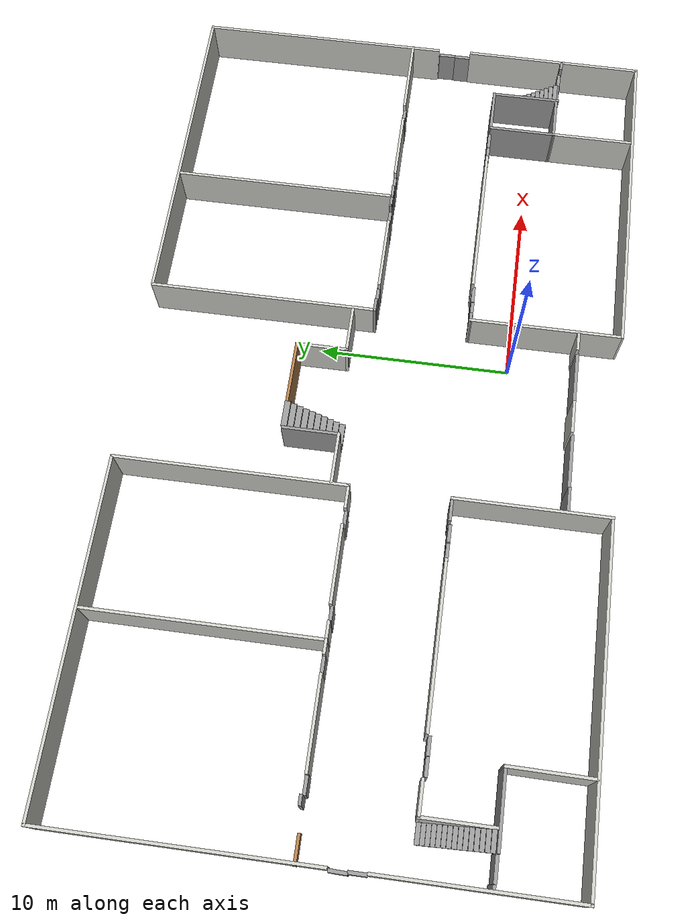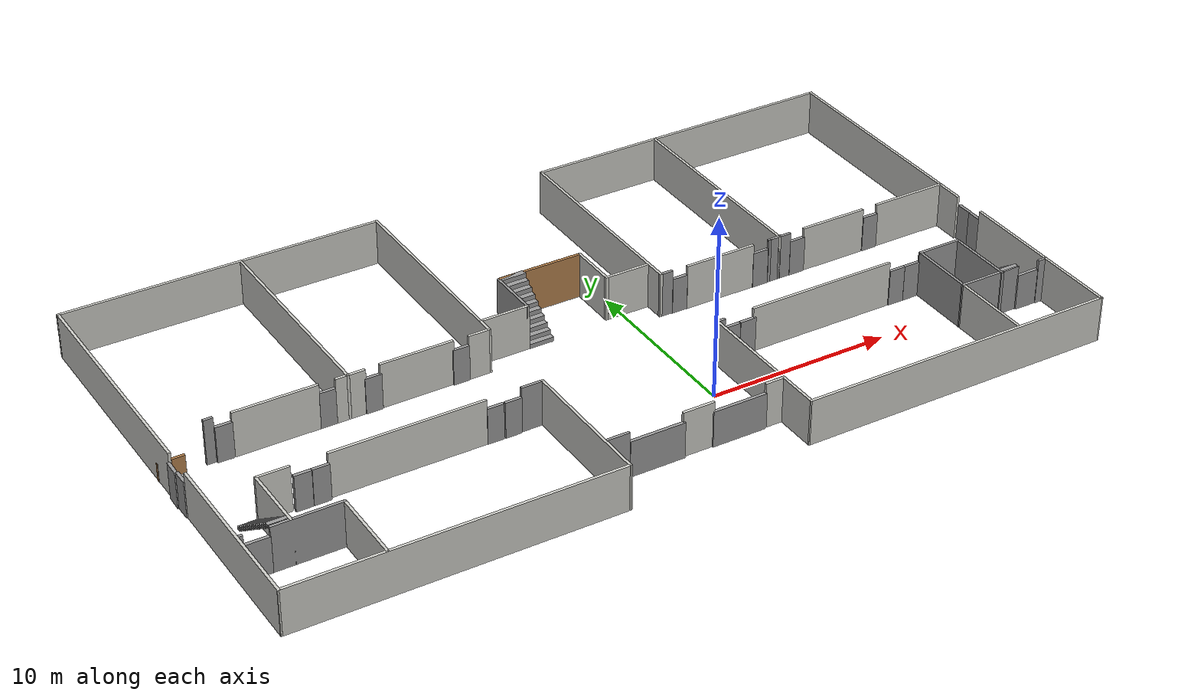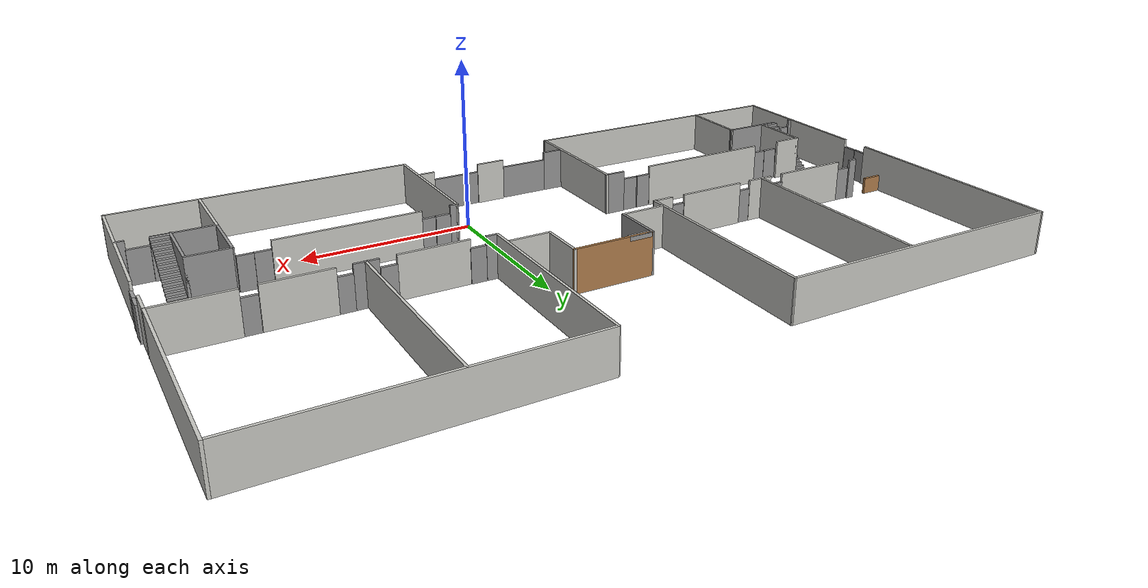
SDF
<?xml version='1.0'?>
<sdf version='1.7'>
  <model name='mts_dept'>
    <pose>-3.28775 6.83696 0 0 -0 0</pose>
    <link name='Door_1'>
      <collision name='Door_1_Collision'>
        <geometry>
          <box>
            <size>0.9 0.17 2</size>
          </box>
        </geometry>
        <pose>0 0 1 0 -0 0</pose>
      </collision>
      <visual name='Door_1_Visual'>
        <pose>0 0 1 0 -0 0</pose>
        <geometry>
          <box>
            <size>0.9 0.17 2</size>
          </box>
        </geometry>
        <material>
          <script>
            <uri>file://media/materials/scripts/gazebo.material</uri>
            <name>Gazebo/Grey</name>
          </script>
        </material>
      </visual>
      <pose>-6.58213 -4.65147 0 0 -0 0</pose>
    </link>
    <link name='Door_13'>
      <collision name='Door_13_Collision'>
        <geometry>
          <box>
            <size>0.9 0.17 2</size>
          </box>
        </geometry>
        <pose>0 0 1 0 -0 0</pose>
      </collision>
      <visual name='Door_13_Visual'>
        <pose>0 0 1 0 -0 0</pose>
        <geometry>
          <box>
            <size>0.9 0.17 2</size>
          </box>
        </geometry>
        <material>
          <script>
            <uri>file://media/materials/scripts/gazebo.material</uri>
            <name>Gazebo/Grey</name>
          </script>
        </material>
      </visual>
      <pose>-22.3834 -2.29202 0 0 -0 -1.5708</pose>
    </link>
    <link name='Door_14'>
      <collision name='Door_14_Collision'>
        <geometry>
          <box>
            <size>0.9 0.17 2</size>
          </box>
        </geometry>
        <pose>0 0 1 0 -0 0</pose>
      </collision>
      <visual name='Door_14_Visual'>
        <pose>0 0 1 0 -0 0</pose>
        <geometry>
          <box>
            <size>0.9 0.17 2</size>
          </box>
        </geometry>
        <material>
          <script>
            <uri>file://media/materials/scripts/gazebo.material</uri>
            <name>Gazebo/Grey</name>
          </script>
        </material>
      </visual>
      <pose>-22.4286 -1.43294 0 0 0 -1.59865</pose>
    </link>
    <link name='Door_15'>
      <collision name='Door_15_Collision'>
        <geometry>
          <box>
            <size>1.25 0.17 2</size>
          </box>
        </geometry>
        <pose>0 0 1 0 -0 0</pose>
      </collision>
      <visual name='Door_15_Visual'>
        <pose>0 0 1 0 -0 0</pose>
        <geometry>
          <box>
            <size>1.25 0.17 2</size>
          </box>
        </geometry>
        <material>
          <script>
            <uri>file://media/materials/scripts/gazebo.material</uri>
            <name>Gazebo/Grey</name>
          </script>
        </material>
      </visual>
      <pose>21.2511 -8.1066 0 0 -0 0</pose>
    </link>
    <link name='Door_16'>
      <collision name='Door_16_Collision'>
        <geometry>
          <box>
            <size>0.9 0.17 2</size>
          </box>
        </geometry>
        <pose>0 0 1 0 -0 0</pose>
      </collision>
      <visual name='Door_16_Visual'>
        <pose>0 0 1 0 -0 0</pose>
        <geometry>
          <box>
            <size>0.9 0.17 2</size>
          </box>
        </geometry>
        <material>
          <script>
            <uri>file://media/materials/scripts/gazebo.material</uri>
            <name>Gazebo/Grey</name>
          </script>
        </material>
      </visual>
      <pose>16.6903 -4.48944 0 0 -0 0</pose>
    </link>
    <link name='Door_17'>
      <collision name='Door_17_Collision'>
        <geometry>
          <box>
            <size>0.9 0.17 2</size>
          </box>
        </geometry>
        <pose>0 0 1 0 -0 0</pose>
      </collision>
      <visual name='Door_17_Visual'>
        <pose>0 0 1 0 -0 0</pose>
        <geometry>
          <box>
            <size>0.9 0.17 2</size>
          </box>
        </geometry>
        <material>
          <script>
            <uri>file://media/materials/scripts/gazebo.material</uri>
            <name>Gazebo/Grey</name>
          </script>
        </material>
      </visual>
      <pose>15.7856 -4.48922 0 0 -0 0</pose>
    </link>
    <link name='Door_18'>
      <collision name='Door_18_Collision'>
        <geometry>
          <box>
            <size>0.9 0.17 2</size>
          </box>
        </geometry>
        <pose>0 0 1 0 -0 0</pose>
      </collision>
      <visual name='Door_18_Visual'>
        <pose>0 0 1 0 -0 0</pose>
        <geometry>
          <box>
            <size>0.9 0.17 2</size>
          </box>
        </geometry>
        <material>
          <script>
            <uri>file://media/materials/scripts/gazebo.material</uri>
            <name>Gazebo/Grey</name>
          </script>
        </material>
      </visual>
      <pose>5.7737 -4.55958 0 0 -0 0</pose>
    </link>
    <link name='Door_19'>
      <collision name='Door_19_Collision'>
        <geometry>
          <box>
            <size>0.9 0.17 2</size>
          </box>
        </geometry>
        <pose>0 0 1 0 -0 0</pose>
      </collision>
      <visual name='Door_19_Visual'>
        <pose>0 0 1 0 -0 0</pose>
        <geometry>
          <box>
            <size>0.9 0.17 2</size>
          </box>
        </geometry>
        <material>
          <script>
            <uri>file://media/materials/scripts/gazebo.material</uri>
            <name>Gazebo/Grey</name>
          </script>
        </material>
      </visual>
      <pose>6.71198 -4.54003 0 0 -0 0</pose>
    </link>
    <link name='Door_2'>
      <collision name='Door_2_Collision'>
        <geometry>
          <box>
            <size>0.9 0.17 2</size>
          </box>
        </geometry>
        <pose>0 0 1 0 -0 0</pose>
      </collision>
      <visual name='Door_2_Visual'>
        <pose>0 0 1 0 -0 0</pose>
        <geometry>
          <box>
            <size>0.9 0.17 2</size>
          </box>
        </geometry>
        <material>
          <script>
            <uri>file://media/materials/scripts/gazebo.material</uri>
            <name>Gazebo/Grey</name>
          </script>
        </material>
      </visual>
      <pose>-7.54552 -4.6498 0 0 -0 0</pose>
    </link>
    <link name='Door_20'>
      <collision name='Door_20_Collision'>
        <geometry>
          <box>
            <size>3 0.17 2</size>
          </box>
        </geometry>
        <pose>0 0 1 0 -0 0</pose>
      </collision>
      <visual name='Door_20_Visual'>
        <pose>0 0 1 0 -0 0</pose>
        <geometry>
          <box>
            <size>3 0.17 2</size>
          </box>
        </geometry>
        <material>
          <script>
            <uri>file://media/materials/scripts/gazebo.material</uri>
            <name>Gazebo/Grey</name>
          </script>
        </material>
      </visual>
      <pose>-2.13617 -10.29 0 0 -0 0</pose>
    </link>
    <link name='Door_21'>
      <collision name='Door_21_Collision'>
        <geometry>
          <box>
            <size>3 0.17 2</size>
          </box>
        </geometry>
        <pose>0 0 1 0 -0 0</pose>
      </collision>
      <visual name='Door_21_Visual'>
        <pose>0 0 1 0 -0 0</pose>
        <geometry>
          <box>
            <size>3 0.17 2</size>
          </box>
        </geometry>
        <material>
          <script>
            <uri>file://media/materials/scripts/gazebo.material</uri>
            <name>Gazebo/Grey</name>
          </script>
        </material>
      </visual>
      <pose>2.44244 -10.26 0 0 -0 0</pose>
    </link>
    <link name='Door_24'>
      <collision name='Door_24_Collision'>
        <geometry>
          <box>
            <size>0.9 0.17 2</size>
          </box>
        </geometry>
        <pose>0 0 1 0 -0 0</pose>
      </collision>
      <visual name='Door_24_Visual'>
        <pose>0 0 1 0 -0 0</pose>
        <geometry>
          <box>
            <size>0.9 0.17 2</size>
          </box>
        </geometry>
        <material>
          <script>
            <uri>file://media/materials/scripts/gazebo.material</uri>
            <name>Gazebo/Grey</name>
          </script>
        </material>
      </visual>
      <pose>13.1152 0.479726 0 0 -0 0</pose>
    </link>
    <link name='Door_25'>
      <collision name='Door_25_Collision'>
        <geometry>
          <box>
            <size>0.9 0.17 2</size>
          </box>
        </geometry>
        <pose>0 0 1 0 -0 0</pose>
      </collision>
      <visual name='Door_25_Visual'>
        <pose>0 0 1 0 -0 0</pose>
        <geometry>
          <box>
            <size>0.9 0.17 2</size>
          </box>
        </geometry>
        <material>
          <script>
            <uri>file://media/materials/scripts/gazebo.material</uri>
            <name>Gazebo/Grey</name>
          </script>
        </material>
      </visual>
      <pose>10.8334 0.469069 0 0 -0 0</pose>
    </link>
    <link name='Door_26'>
      <collision name='Door_26_Collision'>
        <geometry>
          <box>
            <size>0.9 0.17 2</size>
          </box>
        </geometry>
        <pose>0 0 1 0 -0 0</pose>
      </collision>
      <visual name='Door_26_Visual'>
        <pose>0 0 1 0 -0 0</pose>
        <geometry>
          <box>
            <size>0.9 0.17 2</size>
          </box>
        </geometry>
        <material>
          <script>
            <uri>file://media/materials/scripts/gazebo.material</uri>
            <name>Gazebo/Grey</name>
          </script>
        </material>
      </visual>
      <pose>5.99959 0.502503 0 0 -0 0</pose>
    </link>
    <link name='Door_27'>
      <collision name='Door_27_Collision'>
        <geometry>
          <box>
            <size>0.9 0.17 2</size>
          </box>
        </geometry>
        <pose>0 0 1 0 -0 0</pose>
      </collision>
      <visual name='Door_27_Visual'>
        <pose>0 0 1 0 -0 0</pose>
        <geometry>
          <box>
            <size>0.9 0.17 2</size>
          </box>
        </geometry>
        <material>
          <script>
            <uri>file://media/materials/scripts/gazebo.material</uri>
            <name>Gazebo/Grey</name>
          </script>
        </material>
      </visual>
      <pose>17.7287 0.488148 0 0 -0 0</pose>
    </link>
    <link name='Door_28'>
      <collision name='Door_28_Collision'>
        <geometry>
          <box>
            <size>0.9 0.17 2</size>
          </box>
        </geometry>
        <pose>0 0 1 0 -0 0</pose>
      </collision>
      <visual name='Door_28_Visual'>
        <pose>0 0 1 0 -0 0</pose>
        <geometry>
          <box>
            <size>0.9 0.17 2</size>
          </box>
        </geometry>
        <material>
          <script>
            <uri>file://media/materials/scripts/gazebo.material</uri>
            <name>Gazebo/Grey</name>
          </script>
        </material>
      </visual>
      <pose>22.4147 -1.51478 0 0 -0 1.58982</pose>
    </link>
    <link name='Door_29'>
      <collision name='Door_29_Collision'>
        <geometry>
          <box>
            <size>0.9 0.17 2</size>
          </box>
        </geometry>
        <pose>0 0 1 0 -0 0</pose>
      </collision>
      <visual name='Door_29_Visual'>
        <pose>0 0 1 0 -0 0</pose>
        <geometry>
          <box>
            <size>0.9 0.17 2</size>
          </box>
        </geometry>
        <material>
          <script>
            <uri>file://media/materials/scripts/gazebo.material</uri>
            <name>Gazebo/Grey</name>
          </script>
        </material>
      </visual>
      <pose>22.3942 -2.40723 0 0 -0 1.5708</pose>
    </link>
    <link name='Door_3'>
      <collision name='Door_3_Collision'>
        <geometry>
          <box>
            <size>0.9 0.17 2</size>
          </box>
        </geometry>
        <pose>0 0 1 0 -0 0</pose>
      </collision>
      <visual name='Door_3_Visual'>
        <pose>0 0 1 0 -0 0</pose>
        <geometry>
          <box>
            <size>0.9 0.17 2</size>
          </box>
        </geometry>
        <material>
          <script>
            <uri>file://media/materials/scripts/gazebo.material</uri>
            <name>Gazebo/Grey</name>
          </script>
        </material>
      </visual>
      <pose>-16.6533 -4.77247 0 0 -0 0</pose>
    </link>
    <link name='Door_4'>
      <collision name='Door_4_Collision'>
        <geometry>
          <box>
            <size>0.9 0.17 2</size>
          </box>
        </geometry>
        <pose>0 0 1 0 -0 0</pose>
      </collision>
      <visual name='Door_4_Visual'>
        <pose>0 0 1 0 -0 0</pose>
        <geometry>
          <box>
            <size>0.9 0.17 2</size>
          </box>
        </geometry>
        <material>
          <script>
            <uri>file://media/materials/scripts/gazebo.material</uri>
            <name>Gazebo/Grey</name>
          </script>
        </material>
      </visual>
      <pose>-17.5712 -4.7776 0 0 -0 0</pose>
    </link>
    <link name='Door_5'>
      <collision name='Door_5_Collision'>
        <geometry>
          <box>
            <size>1.25 0.17 2</size>
          </box>
        </geometry>
        <pose>0 0 1 0 -0 0</pose>
      </collision>
      <visual name='Door_5_Visual'>
        <pose>0 0 1 0 -0 0</pose>
        <geometry>
          <box>
            <size>1.25 0.17 2</size>
          </box>
        </geometry>
        <material>
          <script>
            <uri>file://media/materials/scripts/gazebo.material</uri>
            <name>Gazebo/Grey</name>
          </script>
        </material>
      </visual>
      <pose>-21.413 -8.25478 0 0 -0 0</pose>
    </link>
    <link name='Door_6'>
      <collision name='Door_6_Collision'>
        <geometry>
          <box>
            <size>0.9 0.17 2</size>
          </box>
        </geometry>
        <pose>0 0 1 0 -0 0</pose>
      </collision>
      <visual name='Door_6_Visual'>
        <pose>0 0 1 0 -0 0</pose>
        <geometry>
          <box>
            <size>0.9 0.17 2</size>
          </box>
        </geometry>
        <material>
          <script>
            <uri>file://media/materials/scripts/gazebo.material</uri>
            <name>Gazebo/Grey</name>
          </script>
        </material>
      </visual>
      <pose>-6.55285 0.494639 0 0 -0 0</pose>
    </link>
    <link name='Door_7'>
      <collision name='Door_7_Collision'>
        <geometry>
          <box>
            <size>0.9 0.17 2</size>
          </box>
        </geometry>
        <pose>0 0 1 0 -0 0</pose>
      </collision>
      <visual name='Door_7_Visual'>
        <pose>0 0 1 0 -0 0</pose>
        <geometry>
          <box>
            <size>0.9 0.17 2</size>
          </box>
        </geometry>
        <material>
          <script>
            <uri>file://media/materials/scripts/gazebo.material</uri>
            <name>Gazebo/Grey</name>
          </script>
        </material>
      </visual>
      <pose>-11.3046 0.493458 0 0 -0 0</pose>
    </link>
    <link name='Door_8'>
      <collision name='Door_8_Collision'>
        <geometry>
          <box>
            <size>0.9 0.17 2</size>
          </box>
        </geometry>
        <pose>0 0 1 0 -0 0</pose>
      </collision>
      <visual name='Door_8_Visual'>
        <pose>0 0 1 0 -0 0</pose>
        <geometry>
          <box>
            <size>0.9 0.17 2</size>
          </box>
        </geometry>
        <material>
          <script>
            <uri>file://media/materials/scripts/gazebo.material</uri>
            <name>Gazebo/Grey</name>
          </script>
        </material>
      </visual>
      <pose>-13.6938 0.528828 0 0 -0 0</pose>
    </link>
    <link name='Door_9'>
      <collision name='Door_9_Collision'>
        <geometry>
          <box>
            <size>0.9 0.17 2</size>
          </box>
        </geometry>
        <pose>0 0 1 0 -0 0</pose>
      </collision>
      <visual name='Door_9_Visual'>
        <pose>0 0 1 0 -0 0</pose>
        <geometry>
          <box>
            <size>0.9 0.17 2</size>
          </box>
        </geometry>
        <material>
          <script>
            <uri>file://media/materials/scripts/gazebo.material</uri>
            <name>Gazebo/Grey</name>
          </script>
        </material>
      </visual>
      <pose>-19.0487 0.509221 0 0 -0 0</pose>
    </link>
    <link name='Stairs_0'>
      <visual name='Stairs_0_Visual_0'>
        <pose>-20.3275 -4.74708 0.083333 0 -0 0</pose>
        <geometry>
          <box>
            <size>1 0.233333 0.166667</size>
          </box>
        </geometry>
        <material>
          <script>
            <uri>file://media/materials/scripts/gazebo.material</uri>
            <name>Gazebo/Grey</name>
          </script>
          <ambient>1 1 1 1</ambient>
        </material>
        <meta>
          <layer>0</layer>
        </meta>
      </visual>
      <collision name='Stairs_0_Collision_0'>
        <geometry>
          <box>
            <size>1 0.233333 0.166667</size>
          </box>
        </geometry>
        <pose>-20.3275 -4.74708 0.083333 0 -0 0</pose>
      </collision>
      <visual name='Stairs_0_Visual_1'>
        <pose>-20.3275 -4.98041 0.25 0 -0 0</pose>
        <geometry>
          <box>
            <size>1 0.233333 0.166667</size>
          </box>
        </geometry>
        <material>
          <script>
            <uri>file://media/materials/scripts/gazebo.material</uri>
            <name>Gazebo/Grey</name>
          </script>
          <ambient>1 1 1 1</ambient>
        </material>
        <meta>
          <layer>0</layer>
        </meta>
      </visual>
      <collision name='Stairs_0_Collision_1'>
        <geometry>
          <box>
            <size>1 0.233333 0.166667</size>
          </box>
        </geometry>
        <pose>-20.3275 -4.98041 0.25 0 -0 0</pose>
      </collision>
      <visual name='Stairs_0_Visual_2'>
        <pose>-20.3275 -5.21374 0.416667 0 -0 0</pose>
        <geometry>
          <box>
            <size>1 0.233333 0.166667</size>
          </box>
        </geometry>
        <material>
          <script>
            <uri>file://media/materials/scripts/gazebo.material</uri>
            <name>Gazebo/Grey</name>
          </script>
          <ambient>1 1 1 1</ambient>
        </material>
        <meta>
          <layer>0</layer>
        </meta>
      </visual>
      <collision name='Stairs_0_Collision_2'>
        <geometry>
          <box>
            <size>1 0.233333 0.166667</size>
          </box>
        </geometry>
        <pose>-20.3275 -5.21374 0.416667 0 -0 0</pose>
      </collision>
      <visual name='Stairs_0_Visual_3'>
        <pose>-20.3275 -5.44708 0.583333 0 -0 0</pose>
        <geometry>
          <box>
            <size>1 0.233333 0.166667</size>
          </box>
        </geometry>
        <material>
          <script>
            <uri>file://media/materials/scripts/gazebo.material</uri>
            <name>Gazebo/Grey</name>
          </script>
          <ambient>1 1 1 1</ambient>
        </material>
        <meta>
          <layer>0</layer>
        </meta>
      </visual>
      <collision name='Stairs_0_Collision_3'>
        <geometry>
          <box>
            <size>1 0.233333 0.166667</size>
          </box>
        </geometry>
        <pose>-20.3275 -5.44708 0.583333 0 -0 0</pose>
      </collision>
      <visual name='Stairs_0_Visual_4'>
        <pose>-20.3275 -5.68041 0.75 0 -0 0</pose>
        <geometry>
          <box>
            <size>1 0.233333 0.166667</size>
          </box>
        </geometry>
        <material>
          <script>
            <uri>file://media/materials/scripts/gazebo.material</uri>
            <name>Gazebo/Grey</name>
          </script>
          <ambient>1 1 1 1</ambient>
        </material>
        <meta>
          <layer>0</layer>
        </meta>
      </visual>
      <collision name='Stairs_0_Collision_4'>
        <geometry>
          <box>
            <size>1 0.233333 0.166667</size>
          </box>
        </geometry>
        <pose>-20.3275 -5.68041 0.75 0 -0 0</pose>
      </collision>
      <visual name='Stairs_0_Visual_5'>
        <pose>-20.3275 -5.91374 0.916667 0 -0 0</pose>
        <geometry>
          <box>
            <size>1 0.233333 0.166667</size>
          </box>
        </geometry>
        <material>
          <script>
            <uri>file://media/materials/scripts/gazebo.material</uri>
            <name>Gazebo/Grey</name>
          </script>
          <ambient>1 1 1 1</ambient>
        </material>
        <meta>
          <layer>0</layer>
        </meta>
      </visual>
      <collision name='Stairs_0_Collision_5'>
        <geometry>
          <box>
            <size>1 0.233333 0.166667</size>
          </box>
        </geometry>
        <pose>-20.3275 -5.91374 0.916667 0 -0 0</pose>
      </collision>
      <visual name='Stairs_0_Visual_6'>
        <pose>-20.3275 -6.14708 1.08333 0 -0 0</pose>
        <geometry>
          <box>
            <size>1 0.233333 0.166667</size>
          </box>
        </geometry>
        <material>
          <script>
            <uri>file://media/materials/scripts/gazebo.material</uri>
            <name>Gazebo/Grey</name>
          </script>
          <ambient>1 1 1 1</ambient>
        </material>
        <meta>
          <layer>0</layer>
        </meta>
      </visual>
      <collision name='Stairs_0_Collision_6'>
        <geometry>
          <box>
            <size>1 0.233333 0.166667</size>
          </box>
        </geometry>
        <pose>-20.3275 -6.14708 1.08333 0 -0 0</pose>
      </collision>
      <visual name='Stairs_0_Visual_7'>
        <pose>-20.3275 -6.38041 1.25 0 -0 0</pose>
        <geometry>
          <box>
            <size>1 0.233333 0.166667</size>
          </box>
        </geometry>
        <material>
          <script>
            <uri>file://media/materials/scripts/gazebo.material</uri>
            <name>Gazebo/Grey</name>
          </script>
          <ambient>1 1 1 1</ambient>
        </material>
        <meta>
          <layer>0</layer>
        </meta>
      </visual>
      <collision name='Stairs_0_Collision_7'>
        <geometry>
          <box>
            <size>1 0.233333 0.166667</size>
          </box>
        </geometry>
        <pose>-20.3275 -6.38041 1.25 0 -0 0</pose>
      </collision>
      <visual name='Stairs_0_Visual_8'>
        <pose>-20.3275 -6.61374 1.41667 0 -0 0</pose>
        <geometry>
          <box>
            <size>1 0.233333 0.166667</size>
          </box>
        </geometry>
        <material>
          <script>
            <uri>file://media/materials/scripts/gazebo.material</uri>
            <name>Gazebo/Grey</name>
          </script>
          <ambient>1 1 1 1</ambient>
        </material>
        <meta>
          <layer>0</layer>
        </meta>
      </visual>
      <collision name='Stairs_0_Collision_8'>
        <geometry>
          <box>
            <size>1 0.233333 0.166667</size>
          </box>
        </geometry>
        <pose>-20.3275 -6.61374 1.41667 0 -0 0</pose>
      </collision>
      <visual name='Stairs_0_Visual_9'>
        <pose>-20.3275 -6.84708 1.58333 0 -0 0</pose>
        <geometry>
          <box>
            <size>1 0.233333 0.166667</size>
          </box>
        </geometry>
        <material>
          <script>
            <uri>file://media/materials/scripts/gazebo.material</uri>
            <name>Gazebo/Grey</name>
          </script>
          <ambient>1 1 1 1</ambient>
        </material>
        <meta>
          <layer>0</layer>
        </meta>
      </visual>
      <collision name='Stairs_0_Collision_9'>
        <geometry>
          <box>
            <size>1 0.233333 0.166667</size>
          </box>
        </geometry>
        <pose>-20.3275 -6.84708 1.58333 0 -0 0</pose>
      </collision>
      <visual name='Stairs_0_Visual_10'>
        <pose>-20.3275 -7.08041 1.75 0 -0 0</pose>
        <geometry>
          <box>
            <size>1 0.233333 0.166667</size>
          </box>
        </geometry>
        <material>
          <script>
            <uri>file://media/materials/scripts/gazebo.material</uri>
            <name>Gazebo/Grey</name>
          </script>
          <ambient>1 1 1 1</ambient>
        </material>
        <meta>
          <layer>0</layer>
        </meta>
      </visual>
      <collision name='Stairs_0_Collision_10'>
        <geometry>
          <box>
            <size>1 0.233333 0.166667</size>
          </box>
        </geometry>
        <pose>-20.3275 -7.08041 1.75 0 -0 0</pose>
      </collision>
      <visual name='Stairs_0_Visual_11'>
        <pose>-20.3275 -7.31374 1.91667 0 -0 0</pose>
        <geometry>
          <box>
            <size>1 0.233333 0.166667</size>
          </box>
        </geometry>
        <material>
          <script>
            <uri>file://media/materials/scripts/gazebo.material</uri>
            <name>Gazebo/Grey</name>
          </script>
          <ambient>1 1 1 1</ambient>
        </material>
        <meta>
          <layer>0</layer>
        </meta>
      </visual>
      <collision name='Stairs_0_Collision_11'>
        <geometry>
          <box>
            <size>1 0.233333 0.166667</size>
          </box>
        </geometry>
        <pose>-20.3275 -7.31374 1.91667 0 -0 0</pose>
      </collision>
      <visual name='Stairs_0_Visual_12'>
        <pose>-20.3275 -7.54708 2.08333 0 -0 0</pose>
        <geometry>
          <box>
            <size>1 0.233333 0.166667</size>
          </box>
        </geometry>
        <material>
          <script>
            <uri>file://media/materials/scripts/gazebo.material</uri>
            <name>Gazebo/Grey</name>
          </script>
          <ambient>1 1 1 1</ambient>
        </material>
        <meta>
          <layer>0</layer>
        </meta>
      </visual>
      <collision name='Stairs_0_Collision_12'>
        <geometry>
          <box>
            <size>1 0.233333 0.166667</size>
          </box>
        </geometry>
        <pose>-20.3275 -7.54708 2.08333 0 -0 0</pose>
      </collision>
      <visual name='Stairs_0_Visual_13'>
        <pose>-20.3275 -7.78041 2.25 0 -0 0</pose>
        <geometry>
          <box>
            <size>1 0.233333 0.166667</size>
          </box>
        </geometry>
        <material>
          <script>
            <uri>file://media/materials/scripts/gazebo.material</uri>
            <name>Gazebo/Grey</name>
          </script>
          <ambient>1 1 1 1</ambient>
        </material>
        <meta>
          <layer>0</layer>
        </meta>
      </visual>
      <collision name='Stairs_0_Collision_13'>
        <geometry>
          <box>
            <size>1 0.233333 0.166667</size>
          </box>
        </geometry>
        <pose>-20.3275 -7.78041 2.25 0 -0 0</pose>
      </collision>
      <visual name='Stairs_0_Visual_14'>
        <pose>-20.3275 -8.01374 2.41667 0 -0 0</pose>
        <geometry>
          <box>
            <size>1 0.233333 0.166667</size>
          </box>
        </geometry>
        <material>
          <script>
            <uri>file://media/materials/scripts/gazebo.material</uri>
            <name>Gazebo/Grey</name>
          </script>
          <ambient>1 1 1 1</ambient>
        </material>
        <meta>
          <layer>0</layer>
        </meta>
      </visual>
      <collision name='Stairs_0_Collision_14'>
        <geometry>
          <box>
            <size>1 0.233333 0.166667</size>
          </box>
        </geometry>
        <pose>-20.3275 -8.01374 2.41667 0 -0 0</pose>
      </collision>
    </link>
    <link name='Stairs_2'>
      <visual name='Stairs_2_Visual_0'>
        <pose>20.1606 -4.63881 0.083333 0 -0 0</pose>
        <geometry>
          <box>
            <size>1 0.233333 0.166667</size>
          </box>
        </geometry>
        <material>
          <script>
            <uri>file://media/materials/scripts/gazebo.material</uri>
            <name>Gazebo/Grey</name>
          </script>
          <ambient>1 1 1 1</ambient>
        </material>
        <meta>
          <layer>0</layer>
        </meta>
      </visual>
      <collision name='Stairs_2_Collision_0'>
        <geometry>
          <box>
            <size>1 0.233333 0.166667</size>
          </box>
        </geometry>
        <pose>20.1606 -4.63881 0.083333 0 -0 0</pose>
      </collision>
      <visual name='Stairs_2_Visual_1'>
        <pose>20.1606 -4.87214 0.25 0 -0 0</pose>
        <geometry>
          <box>
            <size>1 0.233333 0.166667</size>
          </box>
        </geometry>
        <material>
          <script>
            <uri>file://media/materials/scripts/gazebo.material</uri>
            <name>Gazebo/Grey</name>
          </script>
          <ambient>1 1 1 1</ambient>
        </material>
        <meta>
          <layer>0</layer>
        </meta>
      </visual>
      <collision name='Stairs_2_Collision_1'>
        <geometry>
          <box>
            <size>1 0.233333 0.166667</size>
          </box>
        </geometry>
        <pose>20.1606 -4.87214 0.25 0 -0 0</pose>
      </collision>
      <visual name='Stairs_2_Visual_2'>
        <pose>20.1606 -5.10548 0.416667 0 -0 0</pose>
        <geometry>
          <box>
            <size>1 0.233333 0.166667</size>
          </box>
        </geometry>
        <material>
          <script>
            <uri>file://media/materials/scripts/gazebo.material</uri>
            <name>Gazebo/Grey</name>
          </script>
          <ambient>1 1 1 1</ambient>
        </material>
        <meta>
          <layer>0</layer>
        </meta>
      </visual>
      <collision name='Stairs_2_Collision_2'>
        <geometry>
          <box>
            <size>1 0.233333 0.166667</size>
          </box>
        </geometry>
        <pose>20.1606 -5.10548 0.416667 0 -0 0</pose>
      </collision>
      <visual name='Stairs_2_Visual_3'>
        <pose>20.1606 -5.33881 0.583333 0 -0 0</pose>
        <geometry>
          <box>
            <size>1 0.233333 0.166667</size>
          </box>
        </geometry>
        <material>
          <script>
            <uri>file://media/materials/scripts/gazebo.material</uri>
            <name>Gazebo/Grey</name>
          </script>
          <ambient>1 1 1 1</ambient>
        </material>
        <meta>
          <layer>0</layer>
        </meta>
      </visual>
      <collision name='Stairs_2_Collision_3'>
        <geometry>
          <box>
            <size>1 0.233333 0.166667</size>
          </box>
        </geometry>
        <pose>20.1606 -5.33881 0.583333 0 -0 0</pose>
      </collision>
      <visual name='Stairs_2_Visual_4'>
        <pose>20.1606 -5.57214 0.75 0 -0 0</pose>
        <geometry>
          <box>
            <size>1 0.233333 0.166667</size>
          </box>
        </geometry>
        <material>
          <script>
            <uri>file://media/materials/scripts/gazebo.material</uri>
            <name>Gazebo/Grey</name>
          </script>
          <ambient>1 1 1 1</ambient>
        </material>
        <meta>
          <layer>0</layer>
        </meta>
      </visual>
      <collision name='Stairs_2_Collision_4'>
        <geometry>
          <box>
            <size>1 0.233333 0.166667</size>
          </box>
        </geometry>
        <pose>20.1606 -5.57214 0.75 0 -0 0</pose>
      </collision>
      <visual name='Stairs_2_Visual_5'>
        <pose>20.1606 -5.80548 0.916667 0 -0 0</pose>
        <geometry>
          <box>
            <size>1 0.233333 0.166667</size>
          </box>
        </geometry>
        <material>
          <script>
            <uri>file://media/materials/scripts/gazebo.material</uri>
            <name>Gazebo/Grey</name>
          </script>
          <ambient>1 1 1 1</ambient>
        </material>
        <meta>
          <layer>0</layer>
        </meta>
      </visual>
      <collision name='Stairs_2_Collision_5'>
        <geometry>
          <box>
            <size>1 0.233333 0.166667</size>
          </box>
        </geometry>
        <pose>20.1606 -5.80548 0.916667 0 -0 0</pose>
      </collision>
      <visual name='Stairs_2_Visual_6'>
        <pose>20.1606 -6.03881 1.08333 0 -0 0</pose>
        <geometry>
          <box>
            <size>1 0.233333 0.166667</size>
          </box>
        </geometry>
        <material>
          <script>
            <uri>file://media/materials/scripts/gazebo.material</uri>
            <name>Gazebo/Grey</name>
          </script>
          <ambient>1 1 1 1</ambient>
        </material>
        <meta>
          <layer>0</layer>
        </meta>
      </visual>
      <collision name='Stairs_2_Collision_6'>
        <geometry>
          <box>
            <size>1 0.233333 0.166667</size>
          </box>
        </geometry>
        <pose>20.1606 -6.03881 1.08333 0 -0 0</pose>
      </collision>
      <visual name='Stairs_2_Visual_7'>
        <pose>20.1606 -6.27214 1.25 0 -0 0</pose>
        <geometry>
          <box>
            <size>1 0.233333 0.166667</size>
          </box>
        </geometry>
        <material>
          <script>
            <uri>file://media/materials/scripts/gazebo.material</uri>
            <name>Gazebo/Grey</name>
          </script>
          <ambient>1 1 1 1</ambient>
        </material>
        <meta>
          <layer>0</layer>
        </meta>
      </visual>
      <collision name='Stairs_2_Collision_7'>
        <geometry>
          <box>
            <size>1 0.233333 0.166667</size>
          </box>
        </geometry>
        <pose>20.1606 -6.27214 1.25 0 -0 0</pose>
      </collision>
      <visual name='Stairs_2_Visual_8'>
        <pose>20.1606 -6.50548 1.41667 0 -0 0</pose>
        <geometry>
          <box>
            <size>1 0.233333 0.166667</size>
          </box>
        </geometry>
        <material>
          <script>
            <uri>file://media/materials/scripts/gazebo.material</uri>
            <name>Gazebo/Grey</name>
          </script>
          <ambient>1 1 1 1</ambient>
        </material>
        <meta>
          <layer>0</layer>
        </meta>
      </visual>
      <collision name='Stairs_2_Collision_8'>
        <geometry>
          <box>
            <size>1 0.233333 0.166667</size>
          </box>
        </geometry>
        <pose>20.1606 -6.50548 1.41667 0 -0 0</pose>
      </collision>
      <visual name='Stairs_2_Visual_9'>
        <pose>20.1606 -6.73881 1.58333 0 -0 0</pose>
        <geometry>
          <box>
            <size>1 0.233333 0.166667</size>
          </box>
        </geometry>
        <material>
          <script>
            <uri>file://media/materials/scripts/gazebo.material</uri>
            <name>Gazebo/Grey</name>
          </script>
          <ambient>1 1 1 1</ambient>
        </material>
        <meta>
          <layer>0</layer>
        </meta>
      </visual>
      <collision name='Stairs_2_Collision_9'>
        <geometry>
          <box>
            <size>1 0.233333 0.166667</size>
          </box>
        </geometry>
        <pose>20.1606 -6.73881 1.58333 0 -0 0</pose>
      </collision>
      <visual name='Stairs_2_Visual_10'>
        <pose>20.1606 -6.97214 1.75 0 -0 0</pose>
        <geometry>
          <box>
            <size>1 0.233333 0.166667</size>
          </box>
        </geometry>
        <material>
          <script>
            <uri>file://media/materials/scripts/gazebo.material</uri>
            <name>Gazebo/Grey</name>
          </script>
          <ambient>1 1 1 1</ambient>
        </material>
        <meta>
          <layer>0</layer>
        </meta>
      </visual>
      <collision name='Stairs_2_Collision_10'>
        <geometry>
          <box>
            <size>1 0.233333 0.166667</size>
          </box>
        </geometry>
        <pose>20.1606 -6.97214 1.75 0 -0 0</pose>
      </collision>
      <visual name='Stairs_2_Visual_11'>
        <pose>20.1606 -7.20548 1.91667 0 -0 0</pose>
        <geometry>
          <box>
            <size>1 0.233333 0.166667</size>
          </box>
        </geometry>
        <material>
          <script>
            <uri>file://media/materials/scripts/gazebo.material</uri>
            <name>Gazebo/Grey</name>
          </script>
          <ambient>1 1 1 1</ambient>
        </material>
        <meta>
          <layer>0</layer>
        </meta>
      </visual>
      <collision name='Stairs_2_Collision_11'>
        <geometry>
          <box>
            <size>1 0.233333 0.166667</size>
          </box>
        </geometry>
        <pose>20.1606 -7.20548 1.91667 0 -0 0</pose>
      </collision>
      <visual name='Stairs_2_Visual_12'>
        <pose>20.1606 -7.43881 2.08333 0 -0 0</pose>
        <geometry>
          <box>
            <size>1 0.233333 0.166667</size>
          </box>
        </geometry>
        <material>
          <script>
            <uri>file://media/materials/scripts/gazebo.material</uri>
            <name>Gazebo/Grey</name>
          </script>
          <ambient>1 1 1 1</ambient>
        </material>
        <meta>
          <layer>0</layer>
        </meta>
      </visual>
      <collision name='Stairs_2_Collision_12'>
        <geometry>
          <box>
            <size>1 0.233333 0.166667</size>
          </box>
        </geometry>
        <pose>20.1606 -7.43881 2.08333 0 -0 0</pose>
      </collision>
      <visual name='Stairs_2_Visual_13'>
        <pose>20.1606 -7.67214 2.25 0 -0 0</pose>
        <geometry>
          <box>
            <size>1 0.233333 0.166667</size>
          </box>
        </geometry>
        <material>
          <script>
            <uri>file://media/materials/scripts/gazebo.material</uri>
            <name>Gazebo/Grey</name>
          </script>
          <ambient>1 1 1 1</ambient>
        </material>
        <meta>
          <layer>0</layer>
        </meta>
      </visual>
      <collision name='Stairs_2_Collision_13'>
        <geometry>
          <box>
            <size>1 0.233333 0.166667</size>
          </box>
        </geometry>
        <pose>20.1606 -7.67214 2.25 0 -0 0</pose>
      </collision>
      <visual name='Stairs_2_Visual_14'>
        <pose>20.1606 -7.90548 2.41667 0 -0 0</pose>
        <geometry>
          <box>
            <size>1 0.233333 0.166667</size>
          </box>
        </geometry>
        <material>
          <script>
            <uri>file://media/materials/scripts/gazebo.material</uri>
            <name>Gazebo/Grey</name>
          </script>
          <ambient>1 1 1 1</ambient>
        </material>
        <meta>
          <layer>0</layer>
        </meta>
      </visual>
      <collision name='Stairs_2_Collision_14'>
        <geometry>
          <box>
            <size>1 0.233333 0.166667</size>
          </box>
        </geometry>
        <pose>20.1606 -7.90548 2.41667 0 -0 0</pose>
      </collision>
    </link>
    <link name='Stairs_4'>
      <visual name='Stairs_4_Visual_0'>
        <pose>-1.55868 1.45214 0.125 0 0 -3.14159</pose>
        <geometry>
          <box>
            <size>1.36 0.304864 0.25</size>
          </box>
        </geometry>
        <material>
          <script>
            <uri>file://media/materials/scripts/gazebo.material</uri>
            <name>Gazebo/Grey</name>
          </script>
          <ambient>0.368627 0.360784 0.392157 1</ambient>
        </material>
        <meta>
          <layer>0</layer>
        </meta>
      </visual>
      <collision name='Stairs_4_Collision_0'>
        <geometry>
          <box>
            <size>1.36 0.304864 0.25</size>
          </box>
        </geometry>
        <pose>-1.55868 1.45214 0.125 0 0 -3.14159</pose>
      </collision>
      <visual name='Stairs_4_Visual_1'>
        <pose>-1.55868 1.757 0.375 0 0 -3.14159</pose>
        <geometry>
          <box>
            <size>1.36 0.304864 0.25</size>
          </box>
        </geometry>
        <material>
          <script>
            <uri>file://media/materials/scripts/gazebo.material</uri>
            <name>Gazebo/Grey</name>
          </script>
          <ambient>0.368627 0.360784 0.392157 1</ambient>
        </material>
        <meta>
          <layer>0</layer>
        </meta>
      </visual>
      <collision name='Stairs_4_Collision_1'>
        <geometry>
          <box>
            <size>1.36 0.304864 0.25</size>
          </box>
        </geometry>
        <pose>-1.55868 1.757 0.375 0 0 -3.14159</pose>
      </collision>
      <visual name='Stairs_4_Visual_2'>
        <pose>-1.55868 2.06187 0.625 0 0 -3.14159</pose>
        <geometry>
          <box>
            <size>1.36 0.304864 0.25</size>
          </box>
        </geometry>
        <material>
          <script>
            <uri>file://media/materials/scripts/gazebo.material</uri>
            <name>Gazebo/Grey</name>
          </script>
          <ambient>0.368627 0.360784 0.392157 1</ambient>
        </material>
        <meta>
          <layer>0</layer>
        </meta>
      </visual>
      <collision name='Stairs_4_Collision_2'>
        <geometry>
          <box>
            <size>1.36 0.304864 0.25</size>
          </box>
        </geometry>
        <pose>-1.55868 2.06187 0.625 0 0 -3.14159</pose>
      </collision>
      <visual name='Stairs_4_Visual_3'>
        <pose>-1.55868 2.36673 0.875 0 0 -3.14159</pose>
        <geometry>
          <box>
            <size>1.36 0.304864 0.25</size>
          </box>
        </geometry>
        <material>
          <script>
            <uri>file://media/materials/scripts/gazebo.material</uri>
            <name>Gazebo/Grey</name>
          </script>
          <ambient>0.368627 0.360784 0.392157 1</ambient>
        </material>
        <meta>
          <layer>0</layer>
        </meta>
      </visual>
      <collision name='Stairs_4_Collision_3'>
        <geometry>
          <box>
            <size>1.36 0.304864 0.25</size>
          </box>
        </geometry>
        <pose>-1.55868 2.36673 0.875 0 0 -3.14159</pose>
      </collision>
      <visual name='Stairs_4_Visual_4'>
        <pose>-1.55868 2.67159 1.125 0 0 -3.14159</pose>
        <geometry>
          <box>
            <size>1.36 0.304864 0.25</size>
          </box>
        </geometry>
        <material>
          <script>
            <uri>file://media/materials/scripts/gazebo.material</uri>
            <name>Gazebo/Grey</name>
          </script>
          <ambient>0.368627 0.360784 0.392157 1</ambient>
        </material>
        <meta>
          <layer>0</layer>
        </meta>
      </visual>
      <collision name='Stairs_4_Collision_4'>
        <geometry>
          <box>
            <size>1.36 0.304864 0.25</size>
          </box>
        </geometry>
        <pose>-1.55868 2.67159 1.125 0 0 -3.14159</pose>
      </collision>
      <visual name='Stairs_4_Visual_5'>
        <pose>-1.55868 2.97646 1.375 0 0 -3.14159</pose>
        <geometry>
          <box>
            <size>1.36 0.304864 0.25</size>
          </box>
        </geometry>
        <material>
          <script>
            <uri>file://media/materials/scripts/gazebo.material</uri>
            <name>Gazebo/Grey</name>
          </script>
          <ambient>0.368627 0.360784 0.392157 1</ambient>
        </material>
        <meta>
          <layer>0</layer>
        </meta>
      </visual>
      <collision name='Stairs_4_Collision_5'>
        <geometry>
          <box>
            <size>1.36 0.304864 0.25</size>
          </box>
        </geometry>
        <pose>-1.55868 2.97646 1.375 0 0 -3.14159</pose>
      </collision>
      <visual name='Stairs_4_Visual_6'>
        <pose>-1.55868 3.28132 1.625 0 0 -3.14159</pose>
        <geometry>
          <box>
            <size>1.36 0.304864 0.25</size>
          </box>
        </geometry>
        <material>
          <script>
            <uri>file://media/materials/scripts/gazebo.material</uri>
            <name>Gazebo/Grey</name>
          </script>
          <ambient>0.368627 0.360784 0.392157 1</ambient>
        </material>
        <meta>
          <layer>0</layer>
        </meta>
      </visual>
      <collision name='Stairs_4_Collision_6'>
        <geometry>
          <box>
            <size>1.36 0.304864 0.25</size>
          </box>
        </geometry>
        <pose>-1.55868 3.28132 1.625 0 0 -3.14159</pose>
      </collision>
      <visual name='Stairs_4_Visual_7'>
        <pose>-1.55868 3.58619 1.875 0 0 -3.14159</pose>
        <geometry>
          <box>
            <size>1.36 0.304864 0.25</size>
          </box>
        </geometry>
        <material>
          <script>
            <uri>file://media/materials/scripts/gazebo.material</uri>
            <name>Gazebo/Grey</name>
          </script>
          <ambient>0.368627 0.360784 0.392157 1</ambient>
        </material>
        <meta>
          <layer>0</layer>
        </meta>
      </visual>
      <collision name='Stairs_4_Collision_7'>
        <geometry>
          <box>
            <size>1.36 0.304864 0.25</size>
          </box>
        </geometry>
        <pose>-1.55868 3.58619 1.875 0 0 -3.14159</pose>
      </collision>
      <visual name='Stairs_4_Visual_8'>
        <pose>-1.55868 3.89105 2.125 0 0 -3.14159</pose>
        <geometry>
          <box>
            <size>1.36 0.304864 0.25</size>
          </box>
        </geometry>
        <material>
          <script>
            <uri>file://media/materials/scripts/gazebo.material</uri>
            <name>Gazebo/Grey</name>
          </script>
          <ambient>0.368627 0.360784 0.392157 1</ambient>
        </material>
        <meta>
          <layer>0</layer>
        </meta>
      </visual>
      <collision name='Stairs_4_Collision_8'>
        <geometry>
          <box>
            <size>1.36 0.304864 0.25</size>
          </box>
        </geometry>
        <pose>-1.55868 3.89105 2.125 0 0 -3.14159</pose>
      </collision>
      <visual name='Stairs_4_Visual_9'>
        <pose>-1.55868 4.19592 2.375 0 0 -3.14159</pose>
        <geometry>
          <box>
            <size>1.36 0.304864 0.25</size>
          </box>
        </geometry>
        <material>
          <script>
            <uri>file://media/materials/scripts/gazebo.material</uri>
            <name>Gazebo/Grey</name>
          </script>
          <ambient>0.368627 0.360784 0.392157 1</ambient>
        </material>
        <meta>
          <layer>0</layer>
        </meta>
      </visual>
      <collision name='Stairs_4_Collision_9'>
        <geometry>
          <box>
            <size>1.36 0.304864 0.25</size>
          </box>
        </geometry>
        <pose>-1.55868 4.19592 2.375 0 0 -3.14159</pose>
      </collision>
    </link>
    <link name='Wall_104'>
      <collision name='Wall_104_Collision'>
        <geometry>
          <box>
            <size>13.5 0.15 2.5</size>
          </box>
        </geometry>
        <pose>0 0 1.25 0 -0 0</pose>
      </collision>
      <visual name='Wall_104_Visual'>
        <pose>0 0 1.25 0 -0 0</pose>
        <geometry>
          <box>
            <size>13.5 0.15 2.5</size>
          </box>
        </geometry>
        <material>
          <script>
            <uri>file://media/materials/scripts/gazebo.material</uri>
            <name>Gazebo/CeilingTiled</name>
          </script>
          <ambient>1 1 1 1</ambient>
        </material>
        <meta>
          <layer>0</layer>
        </meta>
      </visual>
      <pose>-22.3402 5.7797 0 0 -0 -1.5708</pose>
    </link>
    <link name='Wall_109'>
      <collision name='Wall_109_Collision'>
        <geometry>
          <box>
            <size>9.75 0.15 2.5</size>
          </box>
        </geometry>
        <pose>0 0 1.25 0 -0 0</pose>
      </collision>
      <visual name='Wall_109_Visual'>
        <pose>0 0 1.25 0 -0 0</pose>
        <geometry>
          <box>
            <size>9.75 0.15 2.5</size>
          </box>
        </geometry>
        <material>
          <script>
            <uri>file://media/materials/scripts/gazebo.material</uri>
            <name>Gazebo/CeilingTiled</name>
          </script>
          <ambient>1 1 1 1</ambient>
        </material>
        <meta>
          <layer>0</layer>
        </meta>
      </visual>
      <pose>-22.3402 -7.5953 0 0 -0 1.5708</pose>
    </link>
    <link name='Wall_111'>
      <collision name='Wall_111_Collision'>
        <geometry>
          <box>
            <size>3.5 0.15 2.5</size>
          </box>
        </geometry>
        <pose>0 0 1.25 0 -0 0</pose>
      </collision>
      <visual name='Wall_111_Visual'>
        <pose>0 0 1.25 0 -0 0</pose>
        <geometry>
          <box>
            <size>3.5 0.15 2.5</size>
          </box>
        </geometry>
        <material>
          <script>
            <uri>file://media/materials/scripts/gazebo.material</uri>
            <name>Gazebo/Grey</name>
          </script>
          <ambient>1 1 1 1</ambient>
        </material>
        <meta>
          <layer>0</layer>
        </meta>
      </visual>
      <pose>18.9077 -8.02797 0 0 -0 3.14159</pose>
    </link>
    <link name='Wall_112'>
      <collision name='Wall_112_Collision'>
        <geometry>
          <box>
            <size>4.5 0.15 2.5</size>
          </box>
        </geometry>
        <pose>0 0 1.25 0 -0 0</pose>
      </collision>
      <visual name='Wall_112_Visual'>
        <pose>0 0 1.25 0 -0 0</pose>
        <geometry>
          <box>
            <size>4.5 0.15 2.5</size>
          </box>
        </geometry>
        <material>
          <script>
            <uri>file://media/materials/scripts/gazebo.material</uri>
            <name>Gazebo/CeilingTiled</name>
          </script>
          <ambient>1 1 1 1</ambient>
        </material>
        <meta>
          <layer>0</layer>
        </meta>
      </visual>
      <pose>17.2327 -10.203 0 0 -0 -1.5708</pose>
    </link>
    <link name='Wall_114'>
      <collision name='Wall_114_Collision'>
        <geometry>
          <box>
            <size>0.5 0.15 2.5</size>
          </box>
        </geometry>
        <pose>0 0 1.25 0 -0 0</pose>
      </collision>
      <visual name='Wall_114_Visual'>
        <pose>0 0 1.25 0 -0 0</pose>
        <geometry>
          <box>
            <size>0.5 0.15 2.5</size>
          </box>
        </geometry>
        <material>
          <script>
            <uri>file://media/materials/scripts/gazebo.material</uri>
            <name>Gazebo/Grey</name>
          </script>
          <ambient>1 1 1 1</ambient>
        </material>
        <meta>
          <layer>0</layer>
        </meta>
      </visual>
      <pose>22.0983 -8.14592 0 0 -0 3.14159</pose>
    </link>
    <link name='Wall_116'>
      <collision name='Wall_116_Collision'>
        <geometry>
          <box>
            <size>2.5 0.15 2.5</size>
          </box>
        </geometry>
        <pose>0 0 1.25 0 -0 0</pose>
      </collision>
      <visual name='Wall_116_Visual'>
        <pose>0 0 1.25 0 -0 0</pose>
        <geometry>
          <box>
            <size>2.5 0.15 2.5</size>
          </box>
        </geometry>
        <material>
          <script>
            <uri>file://media/materials/scripts/gazebo.material</uri>
            <name>Gazebo/Grey</name>
          </script>
          <ambient>1 1 1 1</ambient>
        </material>
        <meta>
          <layer>0</layer>
        </meta>
      </visual>
      <pose>18.4248 -4.48944 0 0 -0 3.14159</pose>
    </link>
    <link name='Wall_117'>
      <collision name='Wall_117_Collision'>
        <geometry>
          <box>
            <size>3.68857 0.15 2.5</size>
          </box>
        </geometry>
        <pose>0 0 1.25 0 -0 0</pose>
      </collision>
      <visual name='Wall_117_Visual'>
        <pose>0 0 1.25 0 -0 0</pose>
        <geometry>
          <box>
            <size>3.68857 0.15 2.5</size>
          </box>
        </geometry>
        <material>
          <script>
            <uri>file://media/materials/scripts/gazebo.material</uri>
            <name>Gazebo/Grey</name>
          </script>
          <ambient>1 1 1 1</ambient>
        </material>
        <meta>
          <layer>0</layer>
        </meta>
      </visual>
      <pose>17.2412 -6.2587 0 0 -0 -1.57562</pose>
    </link>
    <link name='Wall_119'>
      <collision name='Wall_119_Collision'>
        <geometry>
          <box>
            <size>8.25 0.15 2.5</size>
          </box>
        </geometry>
        <pose>0 0 1.25 0 -0 0</pose>
      </collision>
      <visual name='Wall_119_Visual'>
        <pose>0 0 1.25 0 -0 0</pose>
        <geometry>
          <box>
            <size>8.25 0.15 2.5</size>
          </box>
        </geometry>
        <material>
          <script>
            <uri>file://media/materials/scripts/gazebo.material</uri>
            <name>Gazebo/CeilingTiled</name>
          </script>
          <ambient>1 1 1 1</ambient>
        </material>
        <meta>
          <layer>0</layer>
        </meta>
      </visual>
      <pose>11.192 -4.46184 0 0 -0 0</pose>
    </link>
    <link name='Wall_122'>
      <collision name='Wall_122_Collision'>
        <geometry>
          <box>
            <size>0.5 0.15 2.5</size>
          </box>
        </geometry>
        <pose>0 0 1.25 0 -0 0</pose>
      </collision>
      <visual name='Wall_122_Visual'>
        <pose>0 0 1.25 0 -0 0</pose>
        <geometry>
          <box>
            <size>0.5 0.15 2.5</size>
          </box>
        </geometry>
        <material>
          <script>
            <uri>file://media/materials/scripts/gazebo.material</uri>
            <name>Gazebo/Grey</name>
          </script>
          <ambient>1 1 1 1</ambient>
        </material>
        <meta>
          <layer>0</layer>
        </meta>
      </visual>
      <pose>5.10893 -4.53609 0 0 -0 0</pose>
    </link>
    <link name='Wall_124'>
      <collision name='Wall_124_Collision'>
        <geometry>
          <box>
            <size>3.75 0.15 2.5</size>
          </box>
        </geometry>
        <pose>0 0 1.25 0 -0 0</pose>
      </collision>
      <visual name='Wall_124_Visual'>
        <pose>0 0 1.25 0 -0 0</pose>
        <geometry>
          <box>
            <size>3.75 0.15 2.5</size>
          </box>
        </geometry>
        <material>
          <script>
            <uri>file://media/materials/scripts/gazebo.material</uri>
            <name>Gazebo/CeilingTiled</name>
          </script>
          <ambient>1 1 1 1</ambient>
        </material>
        <meta>
          <layer>0</layer>
        </meta>
      </visual>
      <pose>-19.7688 -6.45147 0 0 -0 -1.5708</pose>
    </link>
    <link name='Wall_126'>
      <collision name='Wall_126_Collision'>
        <geometry>
          <box>
            <size>3.75 0.15 2.5</size>
          </box>
        </geometry>
        <pose>0 0 1.25 0 -0 0</pose>
      </collision>
      <visual name='Wall_126_Visual'>
        <pose>0 0 1.25 0 -0 0</pose>
        <geometry>
          <box>
            <size>3.75 0.15 2.5</size>
          </box>
        </geometry>
        <material>
          <script>
            <uri>file://media/materials/scripts/gazebo.material</uri>
            <name>Gazebo/Grey</name>
          </script>
          <ambient>1 1 1 1</ambient>
        </material>
        <meta>
          <layer>0</layer>
        </meta>
      </visual>
      <pose>19.5998 -6.28944 0 0 -0 -1.5708</pose>
    </link>
    <link name='Wall_135'>
      <collision name='Wall_135_Collision'>
        <geometry>
          <box>
            <size>2.5 0.15 2.5</size>
          </box>
        </geometry>
        <pose>0 0 1.25 0 -0 0</pose>
      </collision>
      <visual name='Wall_135_Visual'>
        <pose>0 0 1.25 0 -0 0</pose>
        <geometry>
          <box>
            <size>2.5 0.15 2.5</size>
          </box>
        </geometry>
        <material>
          <script>
            <uri>file://media/materials/scripts/gazebo.material</uri>
            <name>Gazebo/CeilingTiled</name>
          </script>
          <ambient>1 1 1 1</ambient>
        </material>
        <meta>
          <layer>0</layer>
        </meta>
      </visual>
      <pose>3.56759 1.65434 0 0 -0 0</pose>
    </link>
    <link name='Wall_137'>
      <collision name='Wall_137_Collision'>
        <geometry>
          <box>
            <size>2.75 0.15 2.5</size>
          </box>
        </geometry>
        <pose>0 0 1.25 0 -0 0</pose>
      </collision>
      <visual name='Wall_137_Visual'>
        <pose>0 0 1.25 0 -0 0</pose>
        <geometry>
          <box>
            <size>2.75 0.15 2.5</size>
          </box>
        </geometry>
        <material>
          <script>
            <uri>file://media/materials/scripts/gazebo.material</uri>
            <name>Gazebo/CeilingTiled</name>
          </script>
          <ambient>1 1 1 1</ambient>
        </material>
        <meta>
          <layer>0</layer>
        </meta>
      </visual>
      <pose>2.39259 2.95433 0 0 -0 1.5708</pose>
    </link>
    <link name='Wall_138'>
      <collision name='Wall_138_Collision'>
        <geometry>
          <box>
            <size>4.75 0.15 2.5</size>
          </box>
        </geometry>
        <pose>0 0 1.25 0 -0 0</pose>
      </collision>
      <visual name='Wall_138_Visual'>
        <pose>0 0 1.25 0 -0 0</pose>
        <geometry>
          <box>
            <size>4.75 0.15 2.5</size>
          </box>
        </geometry>
        <material>
          <script>
            <uri>file://media/materials/scripts/gazebo.material</uri>
            <name>Gazebo/Wood</name>
          </script>
          <ambient>1 1 1 1</ambient>
        </material>
        <meta>
          <layer>0</layer>
        </meta>
      </visual>
      <pose>0.092593 4.25433 0 0 -0 3.14159</pose>
    </link>
    <link name='Wall_141'>
      <collision name='Wall_141_Collision'>
        <geometry>
          <box>
            <size>3 0.15 2.5</size>
          </box>
        </geometry>
        <pose>0 0 1.25 0 -0 0</pose>
      </collision>
      <visual name='Wall_141_Visual'>
        <pose>0 0 1.25 0 -0 0</pose>
        <geometry>
          <box>
            <size>3 0.15 2.5</size>
          </box>
        </geometry>
        <material>
          <script>
            <uri>file://media/materials/scripts/gazebo.material</uri>
            <name>Gazebo/Grey</name>
          </script>
          <ambient>1 1 1 1</ambient>
        </material>
        <meta>
          <layer>0</layer>
        </meta>
      </visual>
      <pose>-2.31448 2.81677 0 0 -0 1.5708</pose>
    </link>
    <link name='Wall_143'>
      <collision name='Wall_143_Collision'>
        <geometry>
          <box>
            <size>2.75 0.15 2.5</size>
          </box>
        </geometry>
        <pose>0 0 1.25 0 -0 0</pose>
      </collision>
      <visual name='Wall_143_Visual'>
        <pose>0 0 1.25 0 -0 0</pose>
        <geometry>
          <box>
            <size>2.75 0.15 2.5</size>
          </box>
        </geometry>
        <material>
          <script>
            <uri>file://media/materials/scripts/gazebo.material</uri>
            <name>Gazebo/CeilingTiled</name>
          </script>
          <ambient>1 1 1 1</ambient>
        </material>
        <meta>
          <layer>0</layer>
        </meta>
      </visual>
      <pose>-3.61449 1.39177 0 0 -0 0</pose>
    </link>
    <link name='Wall_145'>
      <collision name='Wall_145_Collision'>
        <geometry>
          <box>
            <size>1.75 0.15 2.5</size>
          </box>
        </geometry>
        <pose>0 0 1.25 0 -0 0</pose>
      </collision>
      <visual name='Wall_145_Visual'>
        <pose>0 0 1.25 0 -0 0</pose>
        <geometry>
          <box>
            <size>1.75 0.15 2.5</size>
          </box>
        </geometry>
        <material>
          <script>
            <uri>file://media/materials/scripts/gazebo.material</uri>
            <name>Gazebo/CeilingTiled</name>
          </script>
          <ambient>1 1 1 1</ambient>
        </material>
        <meta>
          <layer>0</layer>
        </meta>
      </visual>
      <pose>0.168158 -10.2005 0 0 -0 0</pose>
    </link>
    <link name='Wall_147'>
      <collision name='Wall_147_Collision'>
        <geometry>
          <box>
            <size>1 0.15 2.5</size>
          </box>
        </geometry>
        <pose>0 0 1.25 0 -0 0</pose>
      </collision>
      <visual name='Wall_147_Visual'>
        <pose>0 0 1.25 0 -0 0</pose>
        <geometry>
          <box>
            <size>1 0.15 2.5</size>
          </box>
        </geometry>
        <material>
          <script>
            <uri>file://media/materials/scripts/gazebo.material</uri>
            <name>Gazebo/CeilingTiled</name>
          </script>
          <ambient>1 1 1 1</ambient>
        </material>
        <meta>
          <layer>0</layer>
        </meta>
      </visual>
      <pose>4.41336 -10.2005 0 0 -0 0</pose>
    </link>
    <link name='Wall_149'>
      <collision name='Wall_149_Collision'>
        <geometry>
          <box>
            <size>1.25 0.15 2.5</size>
          </box>
        </geometry>
        <pose>0 0 1.25 0 -0 0</pose>
      </collision>
      <visual name='Wall_149_Visual'>
        <pose>0 0 1.25 0 -0 0</pose>
        <geometry>
          <box>
            <size>1.25 0.15 2.5</size>
          </box>
        </geometry>
        <material>
          <script>
            <uri>file://media/materials/scripts/gazebo.material</uri>
            <name>Gazebo/Grey</name>
          </script>
          <ambient>1 1 1 1</ambient>
        </material>
        <meta>
          <layer>0</layer>
        </meta>
      </visual>
      <pose>-4.26152 -10.26 0 0 -0 3.14159</pose>
    </link>
    <link name='Wall_151'>
      <collision name='Wall_151_Collision'>
        <geometry>
          <box>
            <size>12 0.15 2.5</size>
          </box>
        </geometry>
        <pose>0 0 1.25 0 -0 0</pose>
      </collision>
      <visual name='Wall_151_Visual'>
        <pose>0 0 1.25 0 -0 0</pose>
        <geometry>
          <box>
            <size>12 0.15 2.5</size>
          </box>
        </geometry>
        <material>
          <script>
            <uri>file://media/materials/scripts/gazebo.material</uri>
            <name>Gazebo/CeilingTiled</name>
          </script>
          <ambient>1 1 1 1</ambient>
        </material>
        <meta>
          <layer>0</layer>
        </meta>
      </visual>
      <pose>-12.6013 6.44232 0 0 -0 1.5708</pose>
    </link>
    <link name='Wall_153'>
      <collision name='Wall_153_Collision'>
        <geometry>
          <box>
            <size>4 0.15 2.5</size>
          </box>
        </geometry>
        <pose>0 0 1.25 0 -0 0</pose>
      </collision>
      <visual name='Wall_153_Visual'>
        <pose>0 0 1.25 0 -0 0</pose>
        <geometry>
          <box>
            <size>4 0.15 2.5</size>
          </box>
        </geometry>
        <material>
          <script>
            <uri>file://media/materials/scripts/gazebo.material</uri>
            <name>Gazebo/CeilingTiled</name>
          </script>
          <ambient>1 1 1 1</ambient>
        </material>
        <meta>
          <layer>0</layer>
        </meta>
      </visual>
      <pose>-8.91338 0.557706 0 0 -0 3.14159</pose>
    </link>
    <link name='Wall_155'>
      <collision name='Wall_155_Collision'>
        <geometry>
          <box>
            <size>1 0.15 2.5</size>
          </box>
        </geometry>
        <pose>0 0 1.25 0 -0 0</pose>
      </collision>
      <visual name='Wall_155_Visual'>
        <pose>0 0 1.25 0 -0 0</pose>
        <geometry>
          <box>
            <size>1 0.15 2.5</size>
          </box>
        </geometry>
        <material>
          <script>
            <uri>file://media/materials/scripts/gazebo.material</uri>
            <name>Gazebo/CeilingTiled</name>
          </script>
          <ambient>1 1 1 1</ambient>
        </material>
        <meta>
          <layer>0</layer>
        </meta>
      </visual>
      <pose>-12.1763 0.517323 0 0 -0 0</pose>
    </link>
    <link name='Wall_157'>
      <collision name='Wall_157_Collision'>
        <geometry>
          <box>
            <size>4.5 0.15 2.5</size>
          </box>
        </geometry>
        <pose>0 0 1.25 0 -0 0</pose>
      </collision>
      <visual name='Wall_157_Visual'>
        <pose>0 0 1.25 0 -0 0</pose>
        <geometry>
          <box>
            <size>4.5 0.15 2.5</size>
          </box>
        </geometry>
        <material>
          <script>
            <uri>file://media/materials/scripts/gazebo.material</uri>
            <name>Gazebo/CeilingTiled</name>
          </script>
          <ambient>1 1 1 1</ambient>
        </material>
        <meta>
          <layer>0</layer>
        </meta>
      </visual>
      <pose>-16.3742 0.519684 0 0 -0 0</pose>
    </link>
    <link name='Wall_160'>
      <collision name='Wall_160_Collision'>
        <geometry>
          <box>
            <size>0.75 0.15 2.5</size>
          </box>
        </geometry>
        <pose>0 0 1.25 0 -0 0</pose>
      </collision>
      <visual name='Wall_160_Visual'>
        <pose>0 0 1.25 0 -0 0</pose>
        <geometry>
          <box>
            <size>0.75 0.15 2.5</size>
          </box>
        </geometry>
        <material>
          <script>
            <uri>file://media/materials/scripts/gazebo.material</uri>
            <name>Gazebo/CeilingTiled</name>
          </script>
          <ambient>1 1 1 1</ambient>
        </material>
        <meta>
          <layer>0</layer>
        </meta>
      </visual>
      <pose>-12.9013 0.517323 0 0 -0 3.14159</pose>
    </link>
    <link name='Wall_166'>
      <collision name='Wall_166_Collision'>
        <geometry>
          <box>
            <size>0.5 0.15 2.5</size>
          </box>
        </geometry>
        <pose>0 0 1.25 0 -0 0</pose>
      </collision>
      <visual name='Wall_166_Visual'>
        <pose>0 0 1.25 0 -0 0</pose>
        <geometry>
          <box>
            <size>0.5 0.15 2.5</size>
          </box>
        </geometry>
        <material>
          <script>
            <uri>file://media/materials/scripts/gazebo.material</uri>
            <name>Gazebo/Grey</name>
          </script>
          <ambient>1 1 1 1</ambient>
        </material>
        <meta>
          <layer>0</layer>
        </meta>
      </visual>
      <pose>-19.7405 0.612956 0 0 -0 3.14159</pose>
    </link>
    <link name='Wall_170'>
      <collision name='Wall_170_Collision'>
        <geometry>
          <box>
            <size>12 0.15 2.5</size>
          </box>
        </geometry>
        <pose>0 0 1.25 0 -0 0</pose>
      </collision>
      <visual name='Wall_170_Visual'>
        <pose>0 0 1.25 0 -0 0</pose>
        <geometry>
          <box>
            <size>12 0.15 2.5</size>
          </box>
        </geometry>
        <material>
          <script>
            <uri>file://media/materials/scripts/gazebo.material</uri>
            <name>Gazebo/CeilingTiled</name>
          </script>
          <ambient>1 1 1 1</ambient>
        </material>
        <meta>
          <layer>0</layer>
        </meta>
      </visual>
      <pose>11.9938 6.40566 0 0 -0 1.5708</pose>
    </link>
    <link name='Wall_172'>
      <collision name='Wall_172_Collision'>
        <geometry>
          <box>
            <size>0.75 0.15 2.5</size>
          </box>
        </geometry>
        <pose>0 0 1.25 0 -0 0</pose>
      </collision>
      <visual name='Wall_172_Visual'>
        <pose>0 0 1.25 0 -0 0</pose>
        <geometry>
          <box>
            <size>0.75 0.15 2.5</size>
          </box>
        </geometry>
        <material>
          <script>
            <uri>file://media/materials/scripts/gazebo.material</uri>
            <name>Gazebo/Grey</name>
          </script>
          <ambient>1 1 1 1</ambient>
        </material>
        <meta>
          <layer>0</layer>
        </meta>
      </visual>
      <pose>5.17582 0.518761 0 0 -0 0</pose>
    </link>
    <link name='Wall_174'>
      <collision name='Wall_174_Collision'>
        <geometry>
          <box>
            <size>4 0.15 2.5</size>
          </box>
        </geometry>
        <pose>0 0 1.25 0 -0 0</pose>
      </collision>
      <visual name='Wall_174_Visual'>
        <pose>0 0 1.25 0 -0 0</pose>
        <geometry>
          <box>
            <size>4 0.15 2.5</size>
          </box>
        </geometry>
        <material>
          <script>
            <uri>file://media/materials/scripts/gazebo.material</uri>
            <name>Gazebo/CeilingTiled</name>
          </script>
          <ambient>1 1 1 1</ambient>
        </material>
        <meta>
          <layer>0</layer>
        </meta>
      </visual>
      <pose>8.40586 0.475907 0 0 -0 0</pose>
    </link>
    <link name='Wall_179'>
      <collision name='Wall_179_Collision'>
        <geometry>
          <box>
            <size>0.75 0.15 2.5</size>
          </box>
        </geometry>
        <pose>0 0 1.25 0 -0 0</pose>
      </collision>
      <visual name='Wall_179_Visual'>
        <pose>0 0 1.25 0 -0 0</pose>
        <geometry>
          <box>
            <size>0.75 0.15 2.5</size>
          </box>
        </geometry>
        <material>
          <script>
            <uri>file://media/materials/scripts/gazebo.material</uri>
            <name>Gazebo/Grey</name>
          </script>
          <ambient>1 1 1 1</ambient>
        </material>
        <meta>
          <layer>0</layer>
        </meta>
      </visual>
      <pose>11.6938 0.48066 0 0 -0 3.14159</pose>
    </link>
    <link name='Wall_180'>
      <collision name='Wall_180_Collision'>
        <geometry>
          <box>
            <size>0.15 0.15 2.5</size>
          </box>
        </geometry>
        <pose>0 0 1.25 0 -0 0</pose>
      </collision>
      <visual name='Wall_180_Visual'>
        <pose>0 0 1.25 0 -0 0</pose>
        <geometry>
          <box>
            <size>0.15 0.15 2.5</size>
          </box>
        </geometry>
        <material>
          <script>
            <uri>file://media/materials/scripts/gazebo.material</uri>
            <name>Gazebo/Grey</name>
          </script>
          <ambient>1 1 1 1</ambient>
        </material>
        <meta>
          <layer>0</layer>
        </meta>
      </visual>
      <pose>11.3938 0.48066 0 0 -0 0</pose>
    </link>
    <link name='Wall_182'>
      <collision name='Wall_182_Collision'>
        <geometry>
          <box>
            <size>0.75 0.15 2.5</size>
          </box>
        </geometry>
        <pose>0 0 1.25 0 -0 0</pose>
      </collision>
      <visual name='Wall_182_Visual'>
        <pose>0 0 1.25 0 -0 0</pose>
        <geometry>
          <box>
            <size>0.75 0.15 2.5</size>
          </box>
        </geometry>
        <material>
          <script>
            <uri>file://media/materials/scripts/gazebo.material</uri>
            <name>Gazebo/Grey</name>
          </script>
          <ambient>1 1 1 1</ambient>
        </material>
        <meta>
          <layer>0</layer>
        </meta>
      </visual>
      <pose>12.2938 0.48066 0 0 -0 0</pose>
    </link>
    <link name='Wall_184'>
      <collision name='Wall_184_Collision'>
        <geometry>
          <box>
            <size>3.75 0.15 2.5</size>
          </box>
        </geometry>
        <pose>0 0 1.25 0 -0 0</pose>
      </collision>
      <visual name='Wall_184_Visual'>
        <pose>0 0 1.25 0 -0 0</pose>
        <geometry>
          <box>
            <size>3.75 0.15 2.5</size>
          </box>
        </geometry>
        <material>
          <script>
            <uri>file://media/materials/scripts/gazebo.material</uri>
            <name>Gazebo/CeilingTiled</name>
          </script>
          <ambient>1 1 1 1</ambient>
        </material>
        <meta>
          <layer>0</layer>
        </meta>
      </visual>
      <pose>15.3796 0.498072 0 0 -0 0</pose>
    </link>
    <link name='Wall_186'>
      <collision name='Wall_186_Collision'>
        <geometry>
          <box>
            <size>4.25 0.15 2.5</size>
          </box>
        </geometry>
        <pose>0 0 1.25 0 -0 0</pose>
      </collision>
      <visual name='Wall_186_Visual'>
        <pose>0 0 1.25 0 -0 0</pose>
        <geometry>
          <box>
            <size>4.25 0.15 2.5</size>
          </box>
        </geometry>
        <material>
          <script>
            <uri>file://media/materials/scripts/gazebo.material</uri>
            <name>Gazebo/CeilingTiled</name>
          </script>
          <ambient>1 1 1 1</ambient>
        </material>
        <meta>
          <layer>0</layer>
        </meta>
      </visual>
      <pose>20.2638 0.52797 0 0 -0 0</pose>
    </link>
    <link name='Wall_188'>
      <collision name='Wall_188_Collision'>
        <geometry>
          <box>
            <size>9.71607 0.15 2.5</size>
          </box>
        </geometry>
        <pose>0 0 1.25 0 -0 0</pose>
      </collision>
      <visual name='Wall_188_Visual'>
        <pose>0 0 1.25 0 -0 0</pose>
        <geometry>
          <box>
            <size>9.71607 0.15 2.5</size>
          </box>
        </geometry>
        <material>
          <script>
            <uri>file://media/materials/scripts/gazebo.material</uri>
            <name>Gazebo/CeilingTiled</name>
          </script>
          <ambient>1 1 1 1</ambient>
        </material>
        <meta>
          <layer>0</layer>
        </meta>
      </visual>
      <pose>22.3307 -7.67153 0 0 -0 -1.57688</pose>
    </link>
    <link name='Wall_190'>
      <collision name='Wall_190_Collision'>
        <geometry>
          <box>
            <size>13.5 0.15 2.5</size>
          </box>
        </geometry>
        <pose>0 0 1.25 0 -0 0</pose>
      </collision>
      <visual name='Wall_190_Visual'>
        <pose>0 0 1.25 0 -0 0</pose>
        <geometry>
          <box>
            <size>13.5 0.15 2.5</size>
          </box>
        </geometry>
        <material>
          <script>
            <uri>file://media/materials/scripts/gazebo.material</uri>
            <name>Gazebo/CeilingTiled</name>
          </script>
          <ambient>1 1 1 1</ambient>
        </material>
        <meta>
          <layer>0</layer>
        </meta>
      </visual>
      <pose>22.3016 5.72053 0 0 -0 -1.5708</pose>
    </link>
    <link name='Wall_3'>
      <collision name='Wall_3_Collision'>
        <geometry>
          <box>
            <size>17.5521 0.15 2.5</size>
          </box>
        </geometry>
        <pose>0 0 1.25 0 -0 0</pose>
      </collision>
      <visual name='Wall_3_Visual'>
        <pose>0 0 1.25 0 -0 0</pose>
        <geometry>
          <box>
            <size>17.5521 0.15 2.5</size>
          </box>
        </geometry>
        <material>
          <script>
            <uri>file://media/materials/scripts/gazebo.material</uri>
            <name>Gazebo/CeilingTiled</name>
          </script>
          <ambient>1 1 1 1</ambient>
        </material>
        <meta>
          <layer>0</layer>
        </meta>
      </visual>
      <pose>-13.6392 -12.4213 0 0 -0 -0.002988</pose>
    </link>
    <link name='Wall_33'>
      <collision name='Wall_33_Collision'>
        <geometry>
          <box>
            <size>17.5521 0.15 2.5</size>
          </box>
        </geometry>
        <pose>0 0 1.25 0 -0 0</pose>
      </collision>
      <visual name='Wall_33_Visual'>
        <pose>0 0 1.25 0 -0 0</pose>
        <geometry>
          <box>
            <size>17.5521 0.15 2.5</size>
          </box>
        </geometry>
        <material>
          <script>
            <uri>file://media/materials/scripts/gazebo.material</uri>
            <name>Gazebo/CeilingTiled</name>
          </script>
          <ambient>1 1 1 1</ambient>
        </material>
        <meta>
          <layer>0</layer>
        </meta>
      </visual>
      <pose>-13.6392 12.4287 0 0 -0 -0.002988</pose>
    </link>
    <link name='Wall_35'>
      <collision name='Wall_35_Collision'>
        <geometry>
          <box>
            <size>17.5 0.15 2.5</size>
          </box>
        </geometry>
        <pose>0 0 1.25 0 -0 0</pose>
      </collision>
      <visual name='Wall_35_Visual'>
        <pose>0 0 1.25 0 -0 0</pose>
        <geometry>
          <box>
            <size>17.5 0.15 2.5</size>
          </box>
        </geometry>
        <material>
          <script>
            <uri>file://media/materials/scripts/gazebo.material</uri>
            <name>Gazebo/CeilingTiled</name>
          </script>
          <ambient>1 1 1 1</ambient>
        </material>
        <meta>
          <layer>0</layer>
        </meta>
      </visual>
      <pose>13.6266 12.3955 0 0 -0 3.14159</pose>
    </link>
    <link name='Wall_50'>
      <collision name='Wall_50_Collision'>
        <geometry>
          <box>
            <size>8.0684 0.15 2.5</size>
          </box>
        </geometry>
        <pose>0 0 1.25 0 -0 0</pose>
      </collision>
      <visual name='Wall_50_Visual'>
        <pose>0 0 1.25 0 -0 0</pose>
        <geometry>
          <box>
            <size>8.0684 0.15 2.5</size>
          </box>
        </geometry>
        <material>
          <script>
            <uri>file://media/materials/scripts/gazebo.material</uri>
            <name>Gazebo/CeilingTiled</name>
          </script>
          <ambient>1 1 1 1</ambient>
        </material>
        <meta>
          <layer>0</layer>
        </meta>
      </visual>
      <pose>4.94279 -8.49528 0 0 -0 -1.56856</pose>
    </link>
    <link name='Wall_53'>
      <collision name='Wall_53_Collision'>
        <geometry>
          <box>
            <size>8 0.15 2.5</size>
          </box>
        </geometry>
        <pose>0 0 1.25 0 -0 0</pose>
      </collision>
      <visual name='Wall_53_Visual'>
        <pose>0 0 1.25 0 -0 0</pose>
        <geometry>
          <box>
            <size>8 0.15 2.5</size>
          </box>
        </geometry>
        <material>
          <script>
            <uri>file://media/materials/scripts/gazebo.material</uri>
            <name>Gazebo/CeilingTiled</name>
          </script>
          <ambient>1 1 1 1</ambient>
        </material>
        <meta>
          <layer>0</layer>
        </meta>
      </visual>
      <pose>-4.93823 -8.52229 0 0 -0 1.5708</pose>
    </link>
    <link name='Wall_55'>
      <collision name='Wall_55_Collision'>
        <geometry>
          <box>
            <size>12 0.15 2.5</size>
          </box>
        </geometry>
        <pose>0 0 1.25 0 -0 0</pose>
      </collision>
      <visual name='Wall_55_Visual'>
        <pose>0 0 1.25 0 -0 0</pose>
        <geometry>
          <box>
            <size>12 0.15 2.5</size>
          </box>
        </geometry>
        <material>
          <script>
            <uri>file://media/materials/scripts/gazebo.material</uri>
            <name>Gazebo/CeilingTiled</name>
          </script>
          <ambient>1 1 1 1</ambient>
        </material>
        <meta>
          <layer>0</layer>
        </meta>
      </visual>
      <pose>4.87582 6.44376 0 0 -0 1.5708</pose>
    </link>
    <link name='Wall_57'>
      <collision name='Wall_57_Collision'>
        <geometry>
          <box>
            <size>12.0205 0.15 2.5</size>
          </box>
        </geometry>
        <pose>0 0 1.25 0 -0 0</pose>
      </collision>
      <visual name='Wall_57_Visual'>
        <pose>0 0 1.25 0 -0 0</pose>
        <geometry>
          <box>
            <size>12.0205 0.15 2.5</size>
          </box>
        </geometry>
        <material>
          <script>
            <uri>file://media/materials/scripts/gazebo.material</uri>
            <name>Gazebo/CeilingTiled</name>
          </script>
          <ambient>1 1 1 1</ambient>
        </material>
        <meta>
          <layer>0</layer>
        </meta>
      </visual>
      <pose>-4.9417 6.46748 0 0 -0 1.57021</pose>
    </link>
    <link name='Wall_6'>
      <collision name='Wall_6_Collision'>
        <geometry>
          <box>
            <size>17.5 0.15 2.5</size>
          </box>
        </geometry>
        <pose>0 0 1.25 0 -0 0</pose>
      </collision>
      <visual name='Wall_6_Visual'>
        <pose>0 0 1.25 0 -0 0</pose>
        <geometry>
          <box>
            <size>17.5 0.15 2.5</size>
          </box>
        </geometry>
        <material>
          <script>
            <uri>file://media/materials/scripts/gazebo.material</uri>
            <name>Gazebo/CeilingTiled</name>
          </script>
          <ambient>1 1 1 1</ambient>
        </material>
        <meta>
          <layer>0</layer>
        </meta>
      </visual>
      <pose>13.6266 -12.4545 0 0 -0 0</pose>
    </link>
    <link name='Wall_63'>
      <collision name='Wall_63_Collision'>
        <geometry>
          <box>
            <size>3.75 0.15 2.5</size>
          </box>
        </geometry>
        <pose>0 0 1.25 0 -0 0</pose>
      </collision>
      <visual name='Wall_63_Visual'>
        <pose>0 0 1.25 0 -0 0</pose>
        <geometry>
          <box>
            <size>3.75 0.15 2.5</size>
          </box>
        </geometry>
        <material>
          <script>
            <uri>file://media/materials/scripts/gazebo.material</uri>
            <name>Gazebo/Grey</name>
          </script>
          <ambient>1 1 1 1</ambient>
        </material>
        <meta>
          <layer>0</layer>
        </meta>
      </visual>
      <pose>-18.9346 -8.25147 0 0 -0 0</pose>
    </link>
    <link name='Wall_64'>
      <collision name='Wall_64_Collision'>
        <geometry>
          <box>
            <size>4.25014 0.15 2.5</size>
          </box>
        </geometry>
        <pose>0 0 1.25 0 -0 0</pose>
      </collision>
      <visual name='Wall_64_Visual'>
        <pose>0 0 1.25 0 -0 0</pose>
        <geometry>
          <box>
            <size>4.25014 0.15 2.5</size>
          </box>
        </geometry>
        <material>
          <script>
            <uri>file://media/materials/scripts/gazebo.material</uri>
            <name>Gazebo/CeilingTiled</name>
          </script>
          <ambient>1 1 1 1</ambient>
        </material>
        <meta>
          <layer>0</layer>
        </meta>
      </visual>
      <pose>-17.1517 -10.3015 0 0 -0 -1.57913</pose>
    </link>
    <link name='Wall_66'>
      <collision name='Wall_66_Collision'>
        <geometry>
          <box>
            <size>1.25 0.15 2.5</size>
          </box>
        </geometry>
        <pose>0 0 1.25 0 -0 0</pose>
      </collision>
      <visual name='Wall_66_Visual'>
        <pose>0 0 1.25 0 -0 0</pose>
        <geometry>
          <box>
            <size>1.25 0.15 2.5</size>
          </box>
        </geometry>
        <material>
          <script>
            <uri>file://media/materials/scripts/gazebo.material</uri>
            <name>Gazebo/Grey</name>
          </script>
          <ambient>1 1 1 1</ambient>
        </material>
        <meta>
          <layer>0</layer>
        </meta>
      </visual>
      <pose>-5.48823 -4.59729 0 0 -0 3.14159</pose>
    </link>
    <link name='Wall_69'>
      <collision name='Wall_69_Collision'>
        <geometry>
          <box>
            <size>8.25 0.15 2.5</size>
          </box>
        </geometry>
        <pose>0 0 1.25 0 -0 0</pose>
      </collision>
      <visual name='Wall_69_Visual'>
        <pose>0 0 1.25 0 -0 0</pose>
        <geometry>
          <box>
            <size>8.25 0.15 2.5</size>
          </box>
        </geometry>
        <material>
          <script>
            <uri>file://media/materials/scripts/gazebo.material</uri>
            <name>Gazebo/CeilingTiled</name>
          </script>
          <ambient>1 1 1 1</ambient>
        </material>
        <meta>
          <layer>0</layer>
        </meta>
      </visual>
      <pose>-12.0952 -4.63077 0 0 -0 3.14159</pose>
    </link>
    <link name='Wall_72'>
      <collision name='Wall_72_Collision'>
        <geometry>
          <box>
            <size>1.75 0.15 2.5</size>
          </box>
        </geometry>
        <pose>0 0 1.25 0 -0 0</pose>
      </collision>
      <visual name='Wall_72_Visual'>
        <pose>0 0 1.25 0 -0 0</pose>
        <geometry>
          <box>
            <size>1.75 0.15 2.5</size>
          </box>
        </geometry>
        <material>
          <script>
            <uri>file://media/materials/scripts/gazebo.material</uri>
            <name>Gazebo/CeilingTiled</name>
          </script>
          <ambient>1 1 1 1</ambient>
        </material>
        <meta>
          <layer>0</layer>
        </meta>
      </visual>
      <pose>-18.9688 -4.65147 0 0 -0 0</pose>
    </link>
    <link name='Wall_74'>
      <collision name='Wall_74_Collision'>
        <geometry>
          <box>
            <size>0.25 0.15 2.5</size>
          </box>
        </geometry>
        <pose>0 0 1.25 0 -0 0</pose>
      </collision>
      <visual name='Wall_74_Visual'>
        <pose>0 0 1.25 0 -0 0</pose>
        <geometry>
          <box>
            <size>0.25 0.15 2.5</size>
          </box>
        </geometry>
        <material>
          <script>
            <uri>file://media/materials/scripts/gazebo.material</uri>
            <name>Gazebo/Grey</name>
          </script>
          <ambient>1 1 1 1</ambient>
        </material>
        <meta>
          <layer>0</layer>
        </meta>
      </visual>
      <pose>-22.1809 -8.1864 0 0 -0 3.14159</pose>
    </link>
    <link name='Wall_95'>
      <collision name='Wall_95_Collision'>
        <geometry>
          <box>
            <size>1.4 0.15 1</size>
          </box>
        </geometry>
        <pose>0 0 0.5 0 -0 0</pose>
      </collision>
      <visual name='Wall_95_Visual'>
        <pose>0 0 0.5 0 -0 0</pose>
        <geometry>
          <box>
            <size>1.4 0.15 1</size>
          </box>
        </geometry>
        <material>
          <script>
            <uri>file://media/materials/scripts/gazebo.material</uri>
            <name>Gazebo/Wood</name>
          </script>
          <ambient>1 1 1 1</ambient>
        </material>
        <meta>
          <layer>0</layer>
        </meta>
      </visual>
      <pose>-21.7353 0.54704 0 0 -0 0</pose>
    </link>
    <link name='Wall_98'>
      <collision name='Wall_98_Collision'>
        <geometry>
          <box>
            <size>1.25 0.15 2.5</size>
          </box>
        </geometry>
        <pose>0 0 1.25 0 -0 0</pose>
      </collision>
      <visual name='Wall_98_Visual'>
        <pose>0 0 1.25 0 -0 0</pose>
        <geometry>
          <box>
            <size>1.25 0.15 2.5</size>
          </box>
        </geometry>
        <material>
          <script>
            <uri>file://media/materials/scripts/gazebo.material</uri>
            <name>Gazebo/CeilingTiled</name>
          </script>
          <ambient>1 1 1 1</ambient>
        </material>
        <meta>
          <layer>0</layer>
        </meta>
      </visual>
      <pose>-5.49517 0.532252 0 0 -0 3.14159</pose>
    </link>
    <static>1</static>
  </model>
</sdf>
